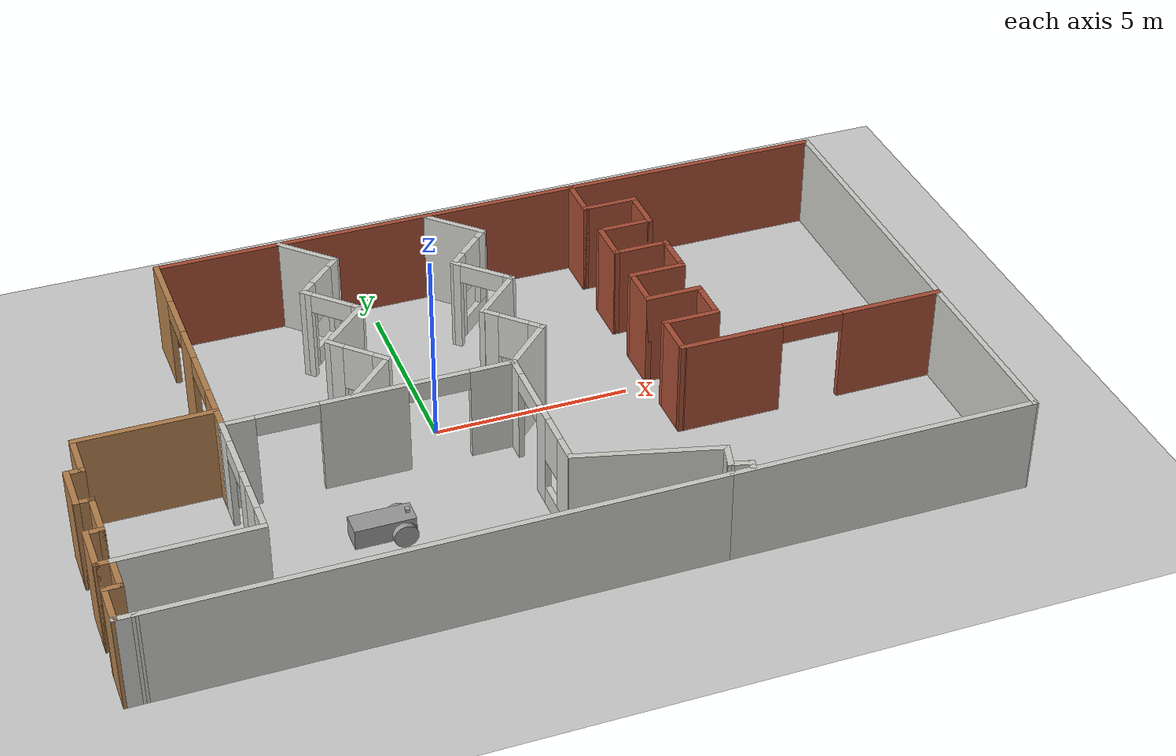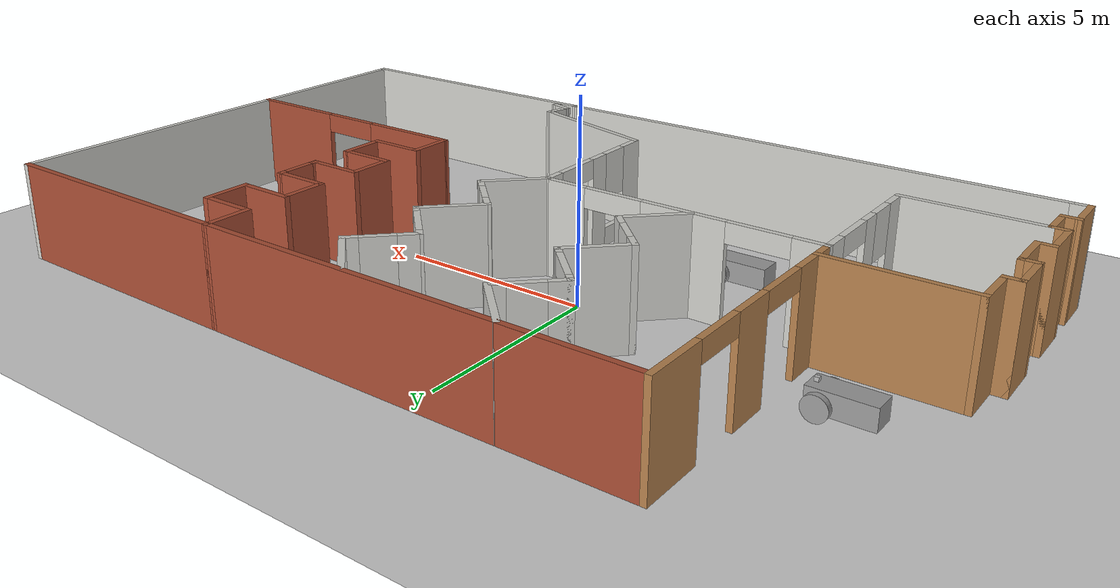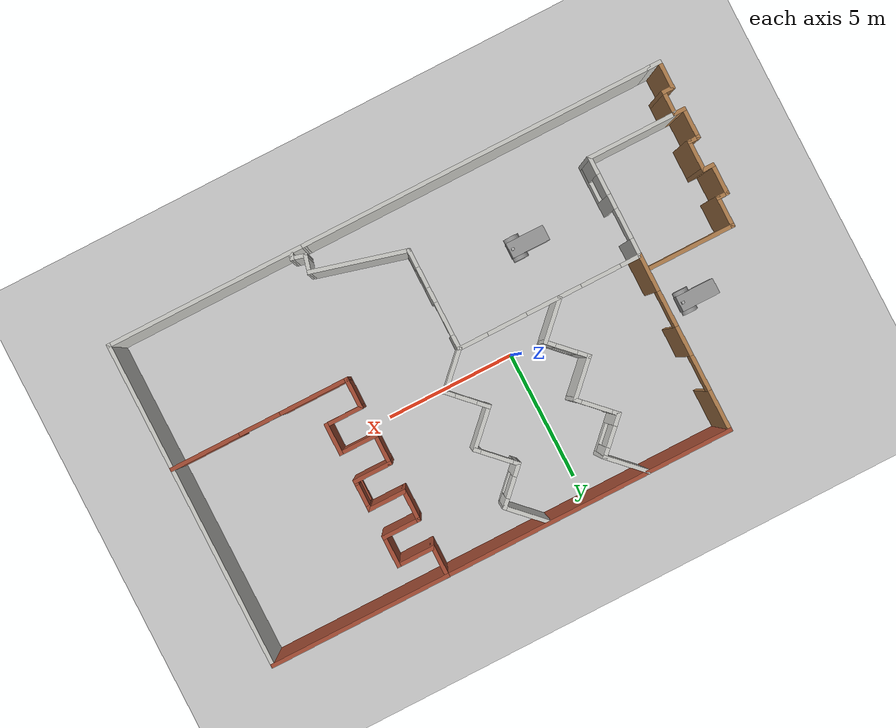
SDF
<sdf version="1.6">
 <world name="default">
  <plugin name="welcome_message" filename="libwelcome_message.so"/>
  <light name="sun" type="directional">
   <pose>0 0 10 0 -0 0</pose>
   <diffuse>0.8 0.8 0.8 1</diffuse>
   <specular>0.2 0.2 0.2 1</specular>
   <attenuation>
    <range>1000</range>
    <constant>0.9</constant>
    <linear>0.01</linear>
    <quadratic>0.001</quadratic>
   </attenuation>
   <direction>-0.5 0.1 -0.9</direction>
  </light>
  <model name="ground_plane">
   <static>1</static>
   <link name="link">
    <collision name="collision">
     <geometry><plane><normal>0 0 1</normal><size>100 100</size></plane></geometry>
     <surface>
      <contact><collide_bitmask>65535</collide_bitmask></contact>
      <friction><ode><mu>100</mu><mu2>50</mu2></ode></friction>
     </surface>
    </collision>
    <visual name="visual">
     <cast_shadows>0</cast_shadows>
     <geometry><plane><normal>0 0 1</normal><size>100 100</size></plane></geometry>
     <material>
      <script><uri>file://media/materials/scripts/gazebo.material</uri><name>Gazebo/Grey</name></script>
     </material>
    </visual>
   </link>
  </model>
  <gravity>0 0 -9.8</gravity>
  <magnetic_field>6e-06 2.3e-05 -4.2e-05</magnetic_field>
  <atmosphere type="adiabatic"/>
  <physics name="default_physics" default="0" type="ode">
   <max_step_size>0.001</max_step_size>
   <real_time_factor>1</real_time_factor>
   <real_time_update_rate>1000</real_time_update_rate>
  </physics>
  <scene><ambient>0.4 0.4 0.4 1</ambient><background>0.7 0.7 0.7 1</background><shadows>1</shadows></scene>
  <spherical_coordinates>
   <surface_model>EARTH_WGS84</surface_model>
   <latitude_deg>0</latitude_deg>
   <longitude_deg>0</longitude_deg>
   <elevation>0</elevation>
   <heading_deg>0</heading_deg>
  </spherical_coordinates>
  <model name="Building">
   <pose>1.68029 -0.499635 0 0 -0 0</pose>
   <link name="Wall_10">
    <collision name="Wall_10_Collision">
     <geometry><box><size>1.75 0.15 2.5</size></box></geometry>
     <pose>0 0 1.25 0 -0 0</pose>
    </collision>
    <visual name="Wall_10_Visual">
     <pose>0 0 1.25 0 -0 0</pose>
     <geometry><box><size>1.75 0.15 2.5</size></box></geometry>
     <material>
      <script><uri>file://media/materials/scripts/gazebo.material</uri><name>Gazebo/CeilingTiled</name></script>
      <ambient>0.819608 0.317647 0.317647 1</ambient>
     </material>
     <meta><layer>0</layer></meta>
    </visual>
    <pose>-3.36491 2.28919 0 0 -0 0.785398</pose>
   </link>
   <link name="Wall_101">
    <collision name="Wall_101_Collision">
     <geometry><box><size>3.69503 0.15 2.5</size></box></geometry>
     <pose>0 0 1.25 0 -0 0</pose>
    </collision>
    <visual name="Wall_101_Visual">
     <pose>0 0 1.25 0 -0 0</pose>
     <geometry><box><size>3.69503 0.15 2.5</size></box></geometry>
     <material>
      <script><uri>file://media/materials/scripts/gazebo.material</uri><name>Gazebo/CeilingTiled</name></script>
      <ambient>0.270588 0.431373 0.760784 1</ambient>
     </material>
     <meta><layer>0</layer></meta>
    </visual>
    <pose>1.71281 -4.90672 0 0 -0 2.88037</pose>
   </link>
   <link name="Wall_103">
    <collision name="Wall_103_Collision">
     <geometry><box><size>3.5 0.15 2.5</size></box></geometry>
     <pose>0 0 1.25 0 -0 0</pose>
    </collision>
    <visual name="Wall_103_Visual">
     <pose>0 0 1.25 0 -0 0</pose>
     <geometry><box><size>3.5 0.15 2.5</size></box></geometry>
     <material>
      <script><uri>file://media/materials/scripts/gazebo.material</uri><name>Gazebo/CeilingTiled</name></script>
      <ambient>0.901961 0.458824 0.458824 1</ambient>
     </material>
     <meta><layer>0</layer></meta>
    </visual>
    <pose>-8.79366 -4.43055 0 0 -0 3.14159</pose>
   </link>
   <link name="Wall_106">
    <collision name="Wall_106_Collision">
     <geometry><box><size>1 0.15 2.5</size></box></geometry>
     <pose>0 0 1.25 0 -0 0</pose>
    </collision>
    <visual name="Wall_106_Visual">
     <pose>0 0 1.25 0 -0 0</pose>
     <geometry><box><size>1 0.15 2.5</size></box></geometry>
     <material>
      <script><uri>file://media/materials/scripts/gazebo.material</uri><name>Gazebo/Wood</name></script>
      <ambient>1 1 1 1</ambient>
     </material>
     <meta><layer>0</layer></meta>
    </visual>
    <pose>-10.4687 -4.85555 0 0 -0 -1.5708</pose>
   </link>
   <link name="Wall_107">
    <collision name="Wall_107_Collision">
     <geometry><box><size>0.5 0.15 2.5</size></box></geometry>
     <pose>0 0 1.25 0 -0 0</pose>
    </collision>
    <visual name="Wall_107_Visual">
     <pose>0 0 1.25 0 -0 0</pose>
     <geometry><box><size>0.5 0.15 2.5</size></box></geometry>
     <material>
      <script><uri>file://media/materials/scripts/gazebo.material</uri><name>Gazebo/Wood</name></script>
      <ambient>1 1 1 1</ambient>
     </material>
     <meta><layer>0</layer></meta>
    </visual>
    <pose>-10.6437 -5.28055 0 0 -0 3.14159</pose>
   </link>
   <link name="Wall_109">
    <collision name="Wall_109_Collision">
     <geometry><box><size>1.14866 0.15 2.5</size></box></geometry>
     <pose>0 0 1.25 0 -0 0</pose>
    </collision>
    <visual name="Wall_109_Visual">
     <pose>0 0 1.25 0 -0 0</pose>
     <geometry><box><size>1.14866 0.15 2.5</size></box></geometry>
     <material>
      <script><uri>file://media/materials/scripts/gazebo.material</uri><name>Gazebo/Wood</name></script>
      <ambient>1 1 1 1</ambient>
     </material>
     <meta><layer>0</layer></meta>
    </visual>
    <pose>-10.8186 -5.77988 0 0 -0 -1.57071</pose>
   </link>
   <link name="Wall_11">
    <pose>-3.36491 3.42056 0 0 -0 2.35619</pose>
    <visual name="Wall_11_Visual_0">
     <pose>-0.725051 0 1.25 0 -0 0</pose>
     <geometry><box><size>0.299898 0.15 2.5</size></box></geometry>
     <material>
      <script><uri>file://media/materials/scripts/gazebo.material</uri><name>Gazebo/CeilingTiled</name></script>
      <ambient>0.819608 0.317647 0.317647 1</ambient>
     </material>
     <meta><layer>0</layer></meta>
    </visual>
    <collision name="Wall_11_Collision_0">
     <geometry><box><size>0.299898 0.15 2.5</size></box></geometry>
     <pose>-0.725051 0 1.25 0 -0 0</pose>
    </collision>
    <visual name="Wall_11_Visual_1">
     <pose>0.716913 0 1.25 0 -0 0</pose>
     <geometry><box><size>0.316173 0.15 2.5</size></box></geometry>
     <material>
      <script><uri>file://media/materials/scripts/gazebo.material</uri><name>Gazebo/CeilingTiled</name></script>
      <ambient>0.819608 0.317647 0.317647 1</ambient>
     </material>
     <meta><layer>0</layer></meta>
    </visual>
    <collision name="Wall_11_Collision_1">
     <geometry><box><size>0.316173 0.15 2.5</size></box></geometry>
     <pose>0.716913 0 1.25 0 -0 0</pose>
    </collision>
    <visual name="Wall_11_Visual_2">
     <pose>-0.008138 0 2.25 0 -0 0</pose>
     <geometry><box><size>1.13393 0.15 0.5</size></box></geometry>
     <material>
      <script><uri>file://media/materials/scripts/gazebo.material</uri><name>Gazebo/CeilingTiled</name></script>
      <ambient>0.819608 0.317647 0.317647 1</ambient>
     </material>
     <meta><layer>0</layer></meta>
    </visual>
    <collision name="Wall_11_Collision_2">
     <geometry><box><size>1.13393 0.15 0.5</size></box></geometry>
     <pose>-0.008138 0 2.25 0 -0 0</pose>
    </collision>
   </link>
   <link name="Wall_110">
    <collision name="Wall_110_Collision">
     <geometry><box><size>0.583483 0.15 2.5</size></box></geometry>
     <pose>0 0 1.25 0 -0 0</pose>
    </collision>
    <visual name="Wall_110_Visual">
     <pose>0 0 1.25 0 -0 0</pose>
     <geometry><box><size>0.583483 0.15 2.5</size></box></geometry>
     <material>
      <script><uri>file://media/materials/scripts/gazebo.material</uri><name>Gazebo/CeilingTiled</name></script>
      <ambient>0.760784 0.662745 0.627451 1</ambient>
     </material>
     <meta><layer>0</layer></meta>
    </visual>
    <pose>-10.6018 -6.27956 0 0 -0 -0.001671</pose>
   </link>
   <link name="Wall_113">
    <collision name="Wall_113_Collision">
     <geometry><box><size>0.5 0.15 2.5</size></box></geometry>
     <pose>0 0 1.25 0 -0 0</pose>
    </collision>
    <visual name="Wall_113_Visual">
     <pose>0 0 1.25 0 -0 0</pose>
     <geometry><box><size>0.5 0.15 2.5</size></box></geometry>
     <material>
      <script><uri>file://media/materials/scripts/gazebo.material</uri><name>Gazebo/Wood</name></script>
      <ambient>1 1 1 1</ambient>
     </material>
     <meta><layer>0</layer></meta>
    </visual>
    <pose>-10.6437 -4.43055 0 0 -0 3.14159</pose>
   </link>
   <link name="Wall_114">
    <collision name="Wall_114_Collision">
     <geometry><box><size>1.25 0.15 2.5</size></box></geometry>
     <pose>0 0 1.25 0 -0 0</pose>
    </collision>
    <visual name="Wall_114_Visual">
     <pose>0 0 1.25 0 -0 0</pose>
     <geometry><box><size>1.25 0.15 2.5</size></box></geometry>
     <material>
      <script><uri>file://media/materials/scripts/gazebo.material</uri><name>Gazebo/Wood</name></script>
      <ambient>1 1 1 1</ambient>
     </material>
     <meta><layer>0</layer></meta>
    </visual>
    <pose>-10.8187 -3.88055 0 0 -0 1.5708</pose>
   </link>
   <link name="Wall_115">
    <collision name="Wall_115_Collision">
     <geometry><box><size>0.5 0.15 2.5</size></box></geometry>
     <pose>0 0 1.25 0 -0 0</pose>
    </collision>
    <visual name="Wall_115_Visual">
     <pose>0 0 1.25 0 -0 0</pose>
     <geometry><box><size>0.5 0.15 2.5</size></box></geometry>
     <material>
      <script><uri>file://media/materials/scripts/gazebo.material</uri><name>Gazebo/Wood</name></script>
      <ambient>1 1 1 1</ambient>
     </material>
     <meta><layer>0</layer></meta>
    </visual>
    <pose>-10.6437 -3.33055 0 0 -0 0</pose>
   </link>
   <link name="Wall_116">
    <collision name="Wall_116_Collision">
     <geometry><box><size>1.25 0.15 2.5</size></box></geometry>
     <pose>0 0 1.25 0 -0 0</pose>
    </collision>
    <visual name="Wall_116_Visual">
     <pose>0 0 1.25 0 -0 0</pose>
     <geometry><box><size>1.25 0.15 2.5</size></box></geometry>
     <material>
      <script><uri>file://media/materials/scripts/gazebo.material</uri><name>Gazebo/Wood</name></script>
      <ambient>1 1 1 1</ambient>
     </material>
     <meta><layer>0</layer></meta>
    </visual>
    <pose>-10.4687 -2.78055 0 0 -0 1.5708</pose>
   </link>
   <link name="Wall_117">
    <collision name="Wall_117_Collision">
     <geometry><box><size>0.5 0.15 2.5</size></box></geometry>
     <pose>0 0 1.25 0 -0 0</pose>
    </collision>
    <visual name="Wall_117_Visual">
     <pose>0 0 1.25 0 -0 0</pose>
     <geometry><box><size>0.5 0.15 2.5</size></box></geometry>
     <material>
      <script><uri>file://media/materials/scripts/gazebo.material</uri><name>Gazebo/Wood</name></script>
      <ambient>1 1 1 1</ambient>
     </material>
     <meta><layer>0</layer></meta>
    </visual>
    <pose>-10.6437 -2.23055 0 0 -0 3.14159</pose>
   </link>
   <link name="Wall_118">
    <collision name="Wall_118_Collision">
     <geometry><box><size>1.25 0.15 2.5</size></box></geometry>
     <pose>0 0 1.25 0 -0 0</pose>
    </collision>
    <visual name="Wall_118_Visual">
     <pose>0 0 1.25 0 -0 0</pose>
     <geometry><box><size>1.25 0.15 2.5</size></box></geometry>
     <material>
      <script><uri>file://media/materials/scripts/gazebo.material</uri><name>Gazebo/Wood</name></script>
      <ambient>1 1 1 1</ambient>
     </material>
     <meta><layer>0</layer></meta>
    </visual>
    <pose>-10.8187 -1.68055 0 0 -0 1.5708</pose>
   </link>
   <link name="Wall_119">
    <collision name="Wall_119_Collision">
     <geometry><box><size>0.5 0.15 2.5</size></box></geometry>
     <pose>0 0 1.25 0 -0 0</pose>
    </collision>
    <visual name="Wall_119_Visual">
     <pose>0 0 1.25 0 -0 0</pose>
     <geometry><box><size>0.5 0.15 2.5</size></box></geometry>
     <material>
      <script><uri>file://media/materials/scripts/gazebo.material</uri><name>Gazebo/Wood</name></script>
      <ambient>1 1 1 1</ambient>
     </material>
     <meta><layer>0</layer></meta>
    </visual>
    <pose>-10.6437 -1.13055 0 0 -0 0</pose>
   </link>
   <link name="Wall_12">
    <pose>-3.36491 4.55193 0 0 -0 0.785398</pose>
    <visual name="Wall_12_Visual_0">
     <pose>-0.61476 0 1.25 0 -0 0</pose>
     <geometry><box><size>0.52048 0.15 2.5</size></box></geometry>
     <material>
      <script><uri>file://media/materials/scripts/gazebo.material</uri><name>Gazebo/CeilingTiled</name></script>
      <ambient>0.819608 0.317647 0.317647 1</ambient>
     </material>
     <meta><layer>0</layer></meta>
    </visual>
    <collision name="Wall_12_Collision_0">
     <geometry><box><size>0.52048 0.15 2.5</size></box></geometry>
     <pose>-0.61476 0 1.25 0 -0 0</pose>
    </collision>
    <visual name="Wall_12_Visual_1">
     <pose>0.26024 0 0.25 0 -0 0</pose>
     <geometry><box><size>1.22952 0.15 0.5</size></box></geometry>
     <material>
      <script><uri>file://media/materials/scripts/gazebo.material</uri><name>Gazebo/CeilingTiled</name></script>
      <ambient>0.819608 0.317647 0.317647 1</ambient>
     </material>
     <meta><layer>0</layer></meta>
    </visual>
    <collision name="Wall_12_Collision_1">
     <geometry><box><size>1.22952 0.15 0.5</size></box></geometry>
     <pose>0.26024 0 0.25 0 -0 0</pose>
    </collision>
    <visual name="Wall_12_Visual_2">
     <pose>0.66024 0 1.5 0 -0 0</pose>
     <geometry><box><size>0.42952 0.15 2</size></box></geometry>
     <material>
      <script><uri>file://media/materials/scripts/gazebo.material</uri><name>Gazebo/CeilingTiled</name></script>
      <ambient>0.819608 0.317647 0.317647 1</ambient>
     </material>
     <meta><layer>0</layer></meta>
    </visual>
    <collision name="Wall_12_Collision_2">
     <geometry><box><size>0.42952 0.15 2</size></box></geometry>
     <pose>0.66024 0 1.5 0 -0 0</pose>
    </collision>
    <visual name="Wall_12_Visual_3">
     <pose>0.04548 0 1.9 0 -0 0</pose>
     <geometry><box><size>0.8 0.15 1.2</size></box></geometry>
     <material>
      <script><uri>file://media/materials/scripts/gazebo.material</uri><name>Gazebo/CeilingTiled</name></script>
      <ambient>0.819608 0.317647 0.317647 1</ambient>
     </material>
     <meta><layer>0</layer></meta>
    </visual>
    <collision name="Wall_12_Collision_3">
     <geometry><box><size>0.8 0.15 1.2</size></box></geometry>
     <pose>0.04548 0 1.9 0 -0 0</pose>
    </collision>
   </link>
   <link name="Wall_120">
    <collision name="Wall_120_Collision">
     <geometry><box><size>1.25 0.15 2.5</size></box></geometry>
     <pose>0 0 1.25 0 -0 0</pose>
    </collision>
    <visual name="Wall_120_Visual">
     <pose>0 0 1.25 0 -0 0</pose>
     <geometry><box><size>1.25 0.15 2.5</size></box></geometry>
     <material>
      <script><uri>file://media/materials/scripts/gazebo.material</uri><name>Gazebo/Wood</name></script>
      <ambient>1 1 1 1</ambient>
     </material>
     <meta><layer>0</layer></meta>
    </visual>
    <pose>-10.4687 -0.580548 0 0 -0 1.5708</pose>
   </link>
   <link name="Wall_121">
    <collision name="Wall_121_Collision">
     <geometry><box><size>3.5 0.15 2.5</size></box></geometry>
     <pose>0 0 1.25 0 -0 0</pose>
    </collision>
    <visual name="Wall_121_Visual">
     <pose>0 0 1.25 0 -0 0</pose>
     <geometry><box><size>3.5 0.15 2.5</size></box></geometry>
     <material>
      <script><uri>file://media/materials/scripts/gazebo.material</uri><name>Gazebo/Wood</name></script>
      <ambient>1 1 1 1</ambient>
     </material>
     <meta><layer>0</layer></meta>
    </visual>
    <pose>-8.79366 -0.030549 0 0 -0 0</pose>
   </link>
   <link name="Wall_14">
    <collision name="Wall_14_Collision">
     <geometry><box><size>1.75 0.15 2.5</size></box></geometry>
     <pose>0 0 1.25 0 -0 0</pose>
    </collision>
    <visual name="Wall_14_Visual">
     <pose>0 0 1.25 0 -0 0</pose>
     <geometry><box><size>1.75 0.15 2.5</size></box></geometry>
     <material>
      <script><uri>file://media/materials/scripts/gazebo.material</uri><name>Gazebo/CeilingTiled</name></script>
      <ambient>0.819608 0.317647 0.317647 1</ambient>
     </material>
     <meta><layer>0</layer></meta>
    </visual>
    <pose>-3.36491 5.6833 0 0 -0 2.35619</pose>
   </link>
   <link name="Wall_18">
    <pose>-7.11866 -2.50555 0 0 -0 -1.5708</pose>
    <visual name="Wall_18_Visual_0">
     <pose>-1.63024 0 1.25 0 -0 0</pose>
     <geometry><box><size>0.739525 0.15 2.5</size></box></geometry>
     <material>
      <script><uri>file://media/materials/scripts/gazebo.material</uri><name>Gazebo/CeilingTiled</name></script>
      <ambient>0.901961 0.458824 0.458824 1</ambient>
     </material>
     <meta><layer>0</layer></meta>
    </visual>
    <collision name="Wall_18_Collision_0">
     <geometry><box><size>0.739525 0.15 2.5</size></box></geometry>
     <pose>-1.63024 0 1.25 0 -0 0</pose>
    </collision>
    <visual name="Wall_18_Visual_1">
     <pose>0.19611 0 1.25 0 -0 0</pose>
     <geometry><box><size>0.547855 0.15 2.5</size></box></geometry>
     <material>
      <script><uri>file://media/materials/scripts/gazebo.material</uri><name>Gazebo/CeilingTiled</name></script>
      <ambient>0.901961 0.458824 0.458824 1</ambient>
     </material>
     <meta><layer>0</layer></meta>
    </visual>
    <collision name="Wall_18_Collision_1">
     <geometry><box><size>0.547855 0.15 2.5</size></box></geometry>
     <pose>0.19611 0 1.25 0 -0 0</pose>
    </collision>
    <visual name="Wall_18_Visual_2">
     <pose>1.23502 0 0.25 0 -0 0</pose>
     <geometry><box><size>1.52996 0.15 0.5</size></box></geometry>
     <material>
      <script><uri>file://media/materials/scripts/gazebo.material</uri><name>Gazebo/CeilingTiled</name></script>
      <ambient>0.901961 0.458824 0.458824 1</ambient>
     </material>
     <meta><layer>0</layer></meta>
    </visual>
    <collision name="Wall_18_Collision_2">
     <geometry><box><size>1.52996 0.15 0.5</size></box></geometry>
     <pose>1.23502 0 0.25 0 -0 0</pose>
    </collision>
    <visual name="Wall_18_Visual_3">
     <pose>1.63502 0 1.5 0 -0 0</pose>
     <geometry><box><size>0.729962 0.15 2</size></box></geometry>
     <material>
      <script><uri>file://media/materials/scripts/gazebo.material</uri><name>Gazebo/CeilingTiled</name></script>
      <ambient>0.901961 0.458824 0.458824 1</ambient>
     </material>
     <meta><layer>0</layer></meta>
    </visual>
    <collision name="Wall_18_Collision_3">
     <geometry><box><size>0.729962 0.15 2</size></box></geometry>
     <pose>1.63502 0 1.5 0 -0 0</pose>
    </collision>
    <visual name="Wall_18_Visual_4">
     <pose>0.870038 0 1.9 0 -0 0</pose>
     <geometry><box><size>0.8 0.15 1.2</size></box></geometry>
     <material>
      <script><uri>file://media/materials/scripts/gazebo.material</uri><name>Gazebo/CeilingTiled</name></script>
      <ambient>0.901961 0.458824 0.458824 1</ambient>
     </material>
     <meta><layer>0</layer></meta>
    </visual>
    <collision name="Wall_18_Collision_4">
     <geometry><box><size>0.8 0.15 1.2</size></box></geometry>
     <pose>0.870038 0 1.9 0 -0 0</pose>
    </collision>
    <visual name="Wall_18_Visual_5">
     <pose>-0.669147 0 2.25 0 -0 0</pose>
     <geometry><box><size>1.18266 0.15 0.5</size></box></geometry>
     <material>
      <script><uri>file://media/materials/scripts/gazebo.material</uri><name>Gazebo/CeilingTiled</name></script>
      <ambient>0.901961 0.458824 0.458824 1</ambient>
     </material>
     <meta><layer>0</layer></meta>
    </visual>
    <collision name="Wall_18_Collision_5">
     <geometry><box><size>1.18266 0.15 0.5</size></box></geometry>
     <pose>-0.669147 0 2.25 0 -0 0</pose>
    </collision>
   </link>
   <link name="Wall_21">
    <pose>-0.018662 -2.50555 0 0 -0 -1.5708</pose>
    <visual name="Wall_21_Visual_0">
     <pose>-1.69808 0 1.25 0 -0 0</pose>
     <geometry><box><size>0.603849 0.15 2.5</size></box></geometry>
     <material>
      <script><uri>file://media/materials/scripts/gazebo.material</uri><name>Gazebo/CeilingTiled</name></script>
      <ambient>0.270588 0.431373 0.760784 1</ambient>
     </material>
     <meta><layer>0</layer></meta>
    </visual>
    <collision name="Wall_21_Collision_0">
     <geometry><box><size>0.603849 0.15 2.5</size></box></geometry>
     <pose>-1.69808 0 1.25 0 -0 0</pose>
    </collision>
    <visual name="Wall_21_Visual_1">
     <pose>0.184804 0 1.25 0 -0 0</pose>
     <geometry><box><size>0.570468 0.15 2.5</size></box></geometry>
     <material>
      <script><uri>file://media/materials/scripts/gazebo.material</uri><name>Gazebo/CeilingTiled</name></script>
      <ambient>0.270588 0.431373 0.760784 1</ambient>
     </material>
     <meta><layer>0</layer></meta>
    </visual>
    <collision name="Wall_21_Collision_1">
     <geometry><box><size>0.570468 0.15 2.5</size></box></geometry>
     <pose>0.184804 0 1.25 0 -0 0</pose>
    </collision>
    <visual name="Wall_21_Visual_2">
     <pose>1.23502 0 0.25 0 -0 0</pose>
     <geometry><box><size>1.52996 0.15 0.5</size></box></geometry>
     <material>
      <script><uri>file://media/materials/scripts/gazebo.material</uri><name>Gazebo/CeilingTiled</name></script>
      <ambient>0.270588 0.431373 0.760784 1</ambient>
     </material>
     <meta><layer>0</layer></meta>
    </visual>
    <collision name="Wall_21_Collision_2">
     <geometry><box><size>1.52996 0.15 0.5</size></box></geometry>
     <pose>1.23502 0 0.25 0 -0 0</pose>
    </collision>
    <visual name="Wall_21_Visual_3">
     <pose>1.63502 0 1.5 0 -0 0</pose>
     <geometry><box><size>0.729962 0.15 2</size></box></geometry>
     <material>
      <script><uri>file://media/materials/scripts/gazebo.material</uri><name>Gazebo/CeilingTiled</name></script>
      <ambient>0.270588 0.431373 0.760784 1</ambient>
     </material>
     <meta><layer>0</layer></meta>
    </visual>
    <collision name="Wall_21_Collision_3">
     <geometry><box><size>0.729962 0.15 2</size></box></geometry>
     <pose>1.63502 0 1.5 0 -0 0</pose>
    </collision>
    <visual name="Wall_21_Visual_4">
     <pose>0.870038 0 1.9 0 -0 0</pose>
     <geometry><box><size>0.8 0.15 1.2</size></box></geometry>
     <material>
      <script><uri>file://media/materials/scripts/gazebo.material</uri><name>Gazebo/CeilingTiled</name></script>
      <ambient>0.270588 0.431373 0.760784 1</ambient>
     </material>
     <meta><layer>0</layer></meta>
    </visual>
    <collision name="Wall_21_Collision_4">
     <geometry><box><size>0.8 0.15 1.2</size></box></geometry>
     <pose>0.870038 0 1.9 0 -0 0</pose>
    </collision>
    <visual name="Wall_21_Visual_5">
     <pose>-0.748291 0 2.25 0 -0 0</pose>
     <geometry><box><size>1.29572 0.15 0.5</size></box></geometry>
     <material>
      <script><uri>file://media/materials/scripts/gazebo.material</uri><name>Gazebo/CeilingTiled</name></script>
      <ambient>0.270588 0.431373 0.760784 1</ambient>
     </material>
     <meta><layer>0</layer></meta>
    </visual>
    <collision name="Wall_21_Collision_5">
     <geometry><box><size>1.29572 0.15 0.5</size></box></geometry>
     <pose>-0.748291 0 2.25 0 -0 0</pose>
    </collision>
   </link>
   <link name="Wall_4">
    <pose>-3.36491 1.15782 0 0 -0 -0.785398</pose>
    <visual name="Wall_4_Visual_0">
     <pose>-0.622738 0 1.25 0 -0 0</pose>
     <geometry><box><size>0.504524 0.15 2.5</size></box></geometry>
     <material>
      <script><uri>file://media/materials/scripts/gazebo.material</uri><name>Gazebo/CeilingTiled</name></script>
      <ambient>0.819608 0.317647 0.317647 1</ambient>
     </material>
     <meta><layer>0</layer></meta>
    </visual>
    <collision name="Wall_4_Collision_0">
     <geometry><box><size>0.504524 0.15 2.5</size></box></geometry>
     <pose>-0.622738 0 1.25 0 -0 0</pose>
    </collision>
    <visual name="Wall_4_Visual_1">
     <pose>0.252262 0 0.25 0 -0 0</pose>
     <geometry><box><size>1.24548 0.15 0.5</size></box></geometry>
     <material>
      <script><uri>file://media/materials/scripts/gazebo.material</uri><name>Gazebo/CeilingTiled</name></script>
      <ambient>0.819608 0.317647 0.317647 1</ambient>
     </material>
     <meta><layer>0</layer></meta>
    </visual>
    <collision name="Wall_4_Collision_1">
     <geometry><box><size>1.24548 0.15 0.5</size></box></geometry>
     <pose>0.252262 0 0.25 0 -0 0</pose>
    </collision>
    <visual name="Wall_4_Visual_2">
     <pose>0.652262 0 1.5 0 -0 0</pose>
     <geometry><box><size>0.445476 0.15 2</size></box></geometry>
     <material>
      <script><uri>file://media/materials/scripts/gazebo.material</uri><name>Gazebo/CeilingTiled</name></script>
      <ambient>0.819608 0.317647 0.317647 1</ambient>
     </material>
     <meta><layer>0</layer></meta>
    </visual>
    <collision name="Wall_4_Collision_2">
     <geometry><box><size>0.445476 0.15 2</size></box></geometry>
     <pose>0.652262 0 1.5 0 -0 0</pose>
    </collision>
    <visual name="Wall_4_Visual_3">
     <pose>0.029524 0 1.9 0 -0 0</pose>
     <geometry><box><size>0.8 0.15 1.2</size></box></geometry>
     <material>
      <script><uri>file://media/materials/scripts/gazebo.material</uri><name>Gazebo/CeilingTiled</name></script>
      <ambient>0.819608 0.317647 0.317647 1</ambient>
     </material>
     <meta><layer>0</layer></meta>
    </visual>
    <collision name="Wall_4_Collision_3">
     <geometry><box><size>0.8 0.15 1.2</size></box></geometry>
     <pose>0.029524 0 1.9 0 -0 0</pose>
    </collision>
   </link>
   <link name="Wall_43">
    <collision name="Wall_43_Collision">
     <geometry><box><size>13.7085 0.15 2.5</size></box></geometry>
     <pose>0 0 1.25 0 -0 0</pose>
    </collision>
    <visual name="Wall_43_Visual">
     <pose>0 0 1.25 0 -0 0</pose>
     <geometry><box><size>13.7085 0.15 2.5</size></box></geometry>
     <material>
      <script><uri>file://media/materials/scripts/gazebo.material</uri><name>Gazebo/CeilingTiled</name></script>
      <ambient>0.760784 0.662745 0.627451 1</ambient>
     </material>
     <meta><layer>0</layer></meta>
    </visual>
    <pose>-3.60582 -6.27971 0 0 -0 3.2e-05</pose>
   </link>
   <link name="Wall_48">
    <collision name="Wall_48_Collision">
     <geometry><box><size>1.75 0.15 2.5</size></box></geometry>
     <pose>0 0 1.25 0 -0 0</pose>
    </collision>
    <visual name="Wall_48_Visual">
     <pose>0 0 1.25 0 -0 0</pose>
     <geometry><box><size>1.75 0.15 2.5</size></box></geometry>
     <material>
      <script><uri>file://media/materials/scripts/gazebo.material</uri><name>Gazebo/CeilingTiled</name></script>
      <ambient>0.447059 0.623529 0.811765 1</ambient>
     </material>
     <meta><layer>0</layer></meta>
    </visual>
    <pose>0.547024 -0.014863 0 0 -0 0.785398</pose>
   </link>
   <link name="Wall_5">
    <collision name="Wall_5_Collision">
     <geometry><box><size>1.75 0.15 2.5</size></box></geometry>
     <pose>0 0 1.25 0 -0 0</pose>
    </collision>
    <visual name="Wall_5_Visual">
     <pose>0 0 1.25 0 -0 0</pose>
     <geometry><box><size>1.75 0.15 2.5</size></box></geometry>
     <material>
      <script><uri>file://media/materials/scripts/gazebo.material</uri><name>Gazebo/CeilingTiled</name></script>
      <ambient>0.819608 0.317647 0.317647 1</ambient>
     </material>
     <meta><layer>0</layer></meta>
    </visual>
    <pose>-3.36491 0.026446 0 0 -0 -2.35619</pose>
   </link>
   <link name="Wall_50">
    <pose>0.551323 1.11651 0 0 -0 2.35238</pose>
    <visual name="Wall_50_Visual_0">
     <pose>-0.655708 0 1.25 0 -0 0</pose>
     <geometry><box><size>0.432515 0.15 2.5</size></box></geometry>
     <material>
      <script><uri>file://media/materials/scripts/gazebo.material</uri><name>Gazebo/CeilingTiled</name></script>
      <ambient>0.447059 0.623529 0.811765 1</ambient>
     </material>
     <meta><layer>0</layer></meta>
    </visual>
    <collision name="Wall_50_Collision_0">
     <geometry><box><size>0.432515 0.15 2.5</size></box></geometry>
     <pose>-0.655708 0 1.25 0 -0 0</pose>
    </collision>
    <visual name="Wall_50_Visual_1">
     <pose>0.216258 0 0.25 0 -0 0</pose>
     <geometry><box><size>1.31142 0.15 0.5</size></box></geometry>
     <material>
      <script><uri>file://media/materials/scripts/gazebo.material</uri><name>Gazebo/CeilingTiled</name></script>
      <ambient>0.447059 0.623529 0.811765 1</ambient>
     </material>
     <meta><layer>0</layer></meta>
    </visual>
    <collision name="Wall_50_Collision_1">
     <geometry><box><size>1.31142 0.15 0.5</size></box></geometry>
     <pose>0.216258 0 0.25 0 -0 0</pose>
    </collision>
    <visual name="Wall_50_Visual_2">
     <pose>0.616258 0 1.5 0 -0 0</pose>
     <geometry><box><size>0.511417 0.15 2</size></box></geometry>
     <material>
      <script><uri>file://media/materials/scripts/gazebo.material</uri><name>Gazebo/CeilingTiled</name></script>
      <ambient>0.447059 0.623529 0.811765 1</ambient>
     </material>
     <meta><layer>0</layer></meta>
    </visual>
    <collision name="Wall_50_Collision_2">
     <geometry><box><size>0.511417 0.15 2</size></box></geometry>
     <pose>0.616258 0 1.5 0 -0 0</pose>
    </collision>
    <visual name="Wall_50_Visual_3">
     <pose>-0.039451 0 1.9 0 -0 0</pose>
     <geometry><box><size>0.8 0.15 1.2</size></box></geometry>
     <material>
      <script><uri>file://media/materials/scripts/gazebo.material</uri><name>Gazebo/CeilingTiled</name></script>
      <ambient>0.447059 0.623529 0.811765 1</ambient>
     </material>
     <meta><layer>0</layer></meta>
    </visual>
    <collision name="Wall_50_Collision_3">
     <geometry><box><size>0.8 0.15 1.2</size></box></geometry>
     <pose>-0.039451 0 1.9 0 -0 0</pose>
    </collision>
   </link>
   <link name="Wall_51">
    <collision name="Wall_51_Collision">
     <geometry><box><size>1.75 0.15 2.5</size></box></geometry>
     <pose>0 0 1.25 0 -0 0</pose>
    </collision>
    <visual name="Wall_51_Visual">
     <pose>0 0 1.25 0 -0 0</pose>
     <geometry><box><size>1.75 0.15 2.5</size></box></geometry>
     <material>
      <script><uri>file://media/materials/scripts/gazebo.material</uri><name>Gazebo/CeilingTiled</name></script>
      <ambient>0.447059 0.623529 0.811765 1</ambient>
     </material>
     <meta><layer>0</layer></meta>
    </visual>
    <pose>0.547024 2.23928 0 0 -0 0.785398</pose>
   </link>
   <link name="Wall_53">
    <pose>0.547024 3.37065 0 0 -0 2.35619</pose>
    <visual name="Wall_53_Visual_0">
     <pose>-0.730842 0 1.25 0 -0 0</pose>
     <geometry><box><size>0.288315 0.15 2.5</size></box></geometry>
     <material>
      <script><uri>file://media/materials/scripts/gazebo.material</uri><name>Gazebo/CeilingTiled</name></script>
      <ambient>0.447059 0.623529 0.811765 1</ambient>
     </material>
     <meta><layer>0</layer></meta>
    </visual>
    <collision name="Wall_53_Collision_0">
     <geometry><box><size>0.288315 0.15 2.5</size></box></geometry>
     <pose>-0.730842 0 1.25 0 -0 0</pose>
    </collision>
    <visual name="Wall_53_Visual_1">
     <pose>0.737705 0 1.25 0 -0 0</pose>
     <geometry><box><size>0.274591 0.15 2.5</size></box></geometry>
     <material>
      <script><uri>file://media/materials/scripts/gazebo.material</uri><name>Gazebo/CeilingTiled</name></script>
      <ambient>0.447059 0.623529 0.811765 1</ambient>
     </material>
     <meta><layer>0</layer></meta>
    </visual>
    <collision name="Wall_53_Collision_1">
     <geometry><box><size>0.274591 0.15 2.5</size></box></geometry>
     <pose>0.737705 0 1.25 0 -0 0</pose>
    </collision>
    <visual name="Wall_53_Visual_2">
     <pose>0.006862 0 2.25 0 -0 0</pose>
     <geometry><box><size>1.18709 0.15 0.5</size></box></geometry>
     <material>
      <script><uri>file://media/materials/scripts/gazebo.material</uri><name>Gazebo/CeilingTiled</name></script>
      <ambient>0.447059 0.623529 0.811765 1</ambient>
     </material>
     <meta><layer>0</layer></meta>
    </visual>
    <collision name="Wall_53_Collision_2">
     <geometry><box><size>1.18709 0.15 0.5</size></box></geometry>
     <pose>0.006862 0 2.25 0 -0 0</pose>
    </collision>
   </link>
   <link name="Wall_54">
    <pose>0.547024 4.50632 0 0 -0 0.789183</pose>
    <visual name="Wall_54_Visual_0">
     <pose>-0.605285 0 1.25 0 -0 0</pose>
     <geometry><box><size>0.545521 0.15 2.5</size></box></geometry>
     <material>
      <script><uri>file://media/materials/scripts/gazebo.material</uri><name>Gazebo/CeilingTiled</name></script>
      <ambient>0.447059 0.623529 0.811765 1</ambient>
     </material>
     <meta><layer>0</layer></meta>
    </visual>
    <collision name="Wall_54_Collision_0">
     <geometry><box><size>0.545521 0.15 2.5</size></box></geometry>
     <pose>-0.605285 0 1.25 0 -0 0</pose>
    </collision>
    <visual name="Wall_54_Visual_1">
     <pose>0.272761 0 0.25 0 -0 0</pose>
     <geometry><box><size>1.21057 0.15 0.5</size></box></geometry>
     <material>
      <script><uri>file://media/materials/scripts/gazebo.material</uri><name>Gazebo/CeilingTiled</name></script>
      <ambient>0.447059 0.623529 0.811765 1</ambient>
     </material>
     <meta><layer>0</layer></meta>
    </visual>
    <collision name="Wall_54_Collision_1">
     <geometry><box><size>1.21057 0.15 0.5</size></box></geometry>
     <pose>0.272761 0 0.25 0 -0 0</pose>
    </collision>
    <visual name="Wall_54_Visual_2">
     <pose>0.672761 0 1.5 0 -0 0</pose>
     <geometry><box><size>0.41057 0.15 2</size></box></geometry>
     <material>
      <script><uri>file://media/materials/scripts/gazebo.material</uri><name>Gazebo/CeilingTiled</name></script>
      <ambient>0.447059 0.623529 0.811765 1</ambient>
     </material>
     <meta><layer>0</layer></meta>
    </visual>
    <collision name="Wall_54_Collision_2">
     <geometry><box><size>0.41057 0.15 2</size></box></geometry>
     <pose>0.672761 0 1.5 0 -0 0</pose>
    </collision>
    <visual name="Wall_54_Visual_3">
     <pose>0.067476 0 1.9 0 -0 0</pose>
     <geometry><box><size>0.8 0.15 1.2</size></box></geometry>
     <material>
      <script><uri>file://media/materials/scripts/gazebo.material</uri><name>Gazebo/CeilingTiled</name></script>
      <ambient>0.447059 0.623529 0.811765 1</ambient>
     </material>
     <meta><layer>0</layer></meta>
    </visual>
    <collision name="Wall_54_Collision_3">
     <geometry><box><size>0.8 0.15 1.2</size></box></geometry>
     <pose>0.067476 0 1.9 0 -0 0</pose>
    </collision>
   </link>
   <link name="Wall_55">
    <collision name="Wall_55_Collision">
     <geometry><box><size>1.75 0.15 2.5</size></box></geometry>
     <pose>0 0 1.25 0 -0 0</pose>
    </collision>
    <visual name="Wall_55_Visual">
     <pose>0 0 1.25 0 -0 0</pose>
     <geometry><box><size>1.75 0.15 2.5</size></box></geometry>
     <material>
      <script><uri>file://media/materials/scripts/gazebo.material</uri><name>Gazebo/CeilingTiled</name></script>
      <ambient>0.447059 0.623529 0.811765 1</ambient>
     </material>
     <meta><layer>0</layer></meta>
    </visual>
    <pose>0.547024 5.64199 0 0 -0 2.35619</pose>
   </link>
   <link name="Wall_61">
    <pose>-7.11866 2.84445 0 0 -0 1.5708</pose>
    <visual name="Wall_61_Visual_0">
     <pose>-2.76325 0 1.25 0 -0 0</pose>
     <geometry><box><size>1.4735 0.15 2.5</size></box></geometry>
     <material>
      <script><uri>file://media/materials/scripts/gazebo.material</uri><name>Gazebo/Wood</name></script>
      <ambient>1 1 1 1</ambient>
     </material>
     <meta><layer>0</layer></meta>
    </visual>
    <collision name="Wall_61_Collision_0">
     <geometry><box><size>1.4735 0.15 2.5</size></box></geometry>
     <pose>-2.76325 0 1.25 0 -0 0</pose>
    </collision>
    <visual name="Wall_61_Visual_1">
     <pose>-0.068748 0 1.25 0 -0 0</pose>
     <geometry><box><size>1.14159 0.15 2.5</size></box></geometry>
     <material>
      <script><uri>file://media/materials/scripts/gazebo.material</uri><name>Gazebo/Wood</name></script>
      <ambient>1 1 1 1</ambient>
     </material>
     <meta><layer>0</layer></meta>
    </visual>
    <collision name="Wall_61_Collision_1">
     <geometry><box><size>1.14159 0.15 2.5</size></box></geometry>
     <pose>-0.068748 0 1.25 0 -0 0</pose>
    </collision>
    <visual name="Wall_61_Visual_2">
     <pose>2.68581 0 1.25 0 -0 0</pose>
     <geometry><box><size>1.62839 0.15 2.5</size></box></geometry>
     <material>
      <script><uri>file://media/materials/scripts/gazebo.material</uri><name>Gazebo/Wood</name></script>
      <ambient>1 1 1 1</ambient>
     </material>
     <meta><layer>0</layer></meta>
    </visual>
    <collision name="Wall_61_Collision_2">
     <geometry><box><size>1.62839 0.15 2.5</size></box></geometry>
     <pose>2.68581 0 1.25 0 -0 0</pose>
    </collision>
    <visual name="Wall_61_Visual_3">
     <pose>-1.33302 0 2.25 0 -0 0</pose>
     <geometry><box><size>1.38696 0.15 0.5</size></box></geometry>
     <material>
      <script><uri>file://media/materials/scripts/gazebo.material</uri><name>Gazebo/Wood</name></script>
      <ambient>1 1 1 1</ambient>
     </material>
     <meta><layer>0</layer></meta>
    </visual>
    <collision name="Wall_61_Collision_3">
     <geometry><box><size>1.38696 0.15 0.5</size></box></geometry>
     <pose>-1.33302 0 2.25 0 -0 0</pose>
    </collision>
    <visual name="Wall_61_Visual_4">
     <pose>1.18683 0 2.25 0 -0 0</pose>
     <geometry><box><size>1.36956 0.15 0.5</size></box></geometry>
     <material>
      <script><uri>file://media/materials/scripts/gazebo.material</uri><name>Gazebo/Wood</name></script>
      <ambient>1 1 1 1</ambient>
     </material>
     <meta><layer>0</layer></meta>
    </visual>
    <collision name="Wall_61_Collision_4">
     <geometry><box><size>1.36956 0.15 0.5</size></box></geometry>
     <pose>1.18683 0 2.25 0 -0 0</pose>
    </collision>
   </link>
   <link name="Wall_62">
    <collision name="Wall_62_Collision">
     <geometry><box><size>11.25 0.15 2.5</size></box></geometry>
     <pose>0 0 1.25 0 -0 0</pose>
    </collision>
    <visual name="Wall_62_Visual">
     <pose>0 0 1.25 0 -0 0</pose>
     <geometry><box><size>11.25 0.15 2.5</size></box></geometry>
     <material>
      <script><uri>file://media/materials/scripts/gazebo.material</uri><name>Gazebo/Bricks</name></script>
      <ambient>1 1 1 1</ambient>
     </material>
     <meta><layer>0</layer></meta>
    </visual>
    <pose>-1.56866 6.26945 0 0 -0 0</pose>
   </link>
   <link name="Wall_64">
    <collision name="Wall_64_Collision">
     <geometry><box><size>1.25 0.15 2.5</size></box></geometry>
     <pose>0 0 1.25 0 -0 0</pose>
    </collision>
    <visual name="Wall_64_Visual">
     <pose>0 0 1.25 0 -0 0</pose>
     <geometry><box><size>1.25 0.15 2.5</size></box></geometry>
     <material>
      <script><uri>file://media/materials/scripts/gazebo.material</uri><name>Gazebo/Bricks</name></script>
      <ambient>1 1 1 1</ambient>
     </material>
     <meta><layer>0</layer></meta>
    </visual>
    <pose>3.98134 5.71945 0 0 -0 -1.5708</pose>
   </link>
   <link name="Wall_65">
    <collision name="Wall_65_Collision">
     <geometry><box><size>1.5 0.15 2.5</size></box></geometry>
     <pose>0 0 1.25 0 -0 0</pose>
    </collision>
    <visual name="Wall_65_Visual">
     <pose>0 0 1.25 0 -0 0</pose>
     <geometry><box><size>1.5 0.15 2.5</size></box></geometry>
     <material>
      <script><uri>file://media/materials/scripts/gazebo.material</uri><name>Gazebo/Bricks</name></script>
      <ambient>1 1 1 1</ambient>
     </material>
     <meta><layer>0</layer></meta>
    </visual>
    <pose>4.65634 5.16945 0 0 -0 0</pose>
   </link>
   <link name="Wall_66">
    <collision name="Wall_66_Collision">
     <geometry><box><size>1.25 0.15 2.5</size></box></geometry>
     <pose>0 0 1.25 0 -0 0</pose>
    </collision>
    <visual name="Wall_66_Visual">
     <pose>0 0 1.25 0 -0 0</pose>
     <geometry><box><size>1.25 0.15 2.5</size></box></geometry>
     <material>
      <script><uri>file://media/materials/scripts/gazebo.material</uri><name>Gazebo/Bricks</name></script>
      <ambient>1 1 1 1</ambient>
     </material>
     <meta><layer>0</layer></meta>
    </visual>
    <pose>5.33134 4.61945 0 0 -0 -1.5708</pose>
   </link>
   <link name="Wall_67">
    <collision name="Wall_67_Collision">
     <geometry><box><size>1.5 0.15 2.5</size></box></geometry>
     <pose>0 0 1.25 0 -0 0</pose>
    </collision>
    <visual name="Wall_67_Visual">
     <pose>0 0 1.25 0 -0 0</pose>
     <geometry><box><size>1.5 0.15 2.5</size></box></geometry>
     <material>
      <script><uri>file://media/materials/scripts/gazebo.material</uri><name>Gazebo/Bricks</name></script>
      <ambient>1 1 1 1</ambient>
     </material>
     <meta><layer>0</layer></meta>
    </visual>
    <pose>4.65634 4.06945 0 0 -0 3.14159</pose>
   </link>
   <link name="Wall_68">
    <collision name="Wall_68_Collision">
     <geometry><box><size>1.25 0.15 2.5</size></box></geometry>
     <pose>0 0 1.25 0 -0 0</pose>
    </collision>
    <visual name="Wall_68_Visual">
     <pose>0 0 1.25 0 -0 0</pose>
     <geometry><box><size>1.25 0.15 2.5</size></box></geometry>
     <material>
      <script><uri>file://media/materials/scripts/gazebo.material</uri><name>Gazebo/Bricks</name></script>
      <ambient>1 1 1 1</ambient>
     </material>
     <meta><layer>0</layer></meta>
    </visual>
    <pose>3.98134 3.51945 0 0 -0 -1.5708</pose>
   </link>
   <link name="Wall_69">
    <collision name="Wall_69_Collision">
     <geometry><box><size>1.5 0.15 2.5</size></box></geometry>
     <pose>0 0 1.25 0 -0 0</pose>
    </collision>
    <visual name="Wall_69_Visual">
     <pose>0 0 1.25 0 -0 0</pose>
     <geometry><box><size>1.5 0.15 2.5</size></box></geometry>
     <material>
      <script><uri>file://media/materials/scripts/gazebo.material</uri><name>Gazebo/Bricks</name></script>
      <ambient>1 1 1 1</ambient>
     </material>
     <meta><layer>0</layer></meta>
    </visual>
    <pose>4.65634 2.96945 0 0 -0 0</pose>
   </link>
   <link name="Wall_7">
    <pose>-3.56866 -0.580548 0 0 -0 0</pose>
    <visual name="Wall_7_Visual_0">
     <pose>-3.20048 0 1.25 0 -0 0</pose>
     <geometry><box><size>0.849038 0.15 2.5</size></box></geometry>
     <material>
      <script><uri>file://media/materials/scripts/gazebo.material</uri><name>Gazebo/CeilingTiled</name></script>
      <ambient>0.901961 0.458824 0.458824 1</ambient>
     </material>
     <meta><layer>0</layer></meta>
    </visual>
    <collision name="Wall_7_Collision_0">
     <geometry><box><size>0.849038 0.15 2.5</size></box></geometry>
     <pose>-3.20048 0 1.25 0 -0 0</pose>
    </collision>
    <visual name="Wall_7_Visual_1">
     <pose>-0.160732 0 1.25 0 -0 0</pose>
     <geometry><box><size>2.14454 0.15 2.5</size></box></geometry>
     <material>
      <script><uri>file://media/materials/scripts/gazebo.material</uri><name>Gazebo/CeilingTiled</name></script>
      <ambient>0.901961 0.458824 0.458824 1</ambient>
     </material>
     <meta><layer>0</layer></meta>
    </visual>
    <collision name="Wall_7_Collision_1">
     <geometry><box><size>2.14454 0.15 2.5</size></box></geometry>
     <pose>-0.160732 0 1.25 0 -0 0</pose>
    </collision>
    <visual name="Wall_7_Visual_2">
     <pose>3.03227 0 1.25 0 -0 0</pose>
     <geometry><box><size>1.18546 0.15 2.5</size></box></geometry>
     <material>
      <script><uri>file://media/materials/scripts/gazebo.material</uri><name>Gazebo/CeilingTiled</name></script>
      <ambient>0.901961 0.458824 0.458824 1</ambient>
     </material>
     <meta><layer>0</layer></meta>
    </visual>
    <collision name="Wall_7_Collision_2">
     <geometry><box><size>1.18546 0.15 2.5</size></box></geometry>
     <pose>3.03227 0 1.25 0 -0 0</pose>
    </collision>
    <visual name="Wall_7_Visual_3">
     <pose>-2.00448 0 2.25 0 -0 0</pose>
     <geometry><box><size>1.54296 0.15 0.5</size></box></geometry>
     <material>
      <script><uri>file://media/materials/scripts/gazebo.material</uri><name>Gazebo/CeilingTiled</name></script>
      <ambient>0.901961 0.458824 0.458824 1</ambient>
     </material>
     <meta><layer>0</layer></meta>
    </visual>
    <collision name="Wall_7_Collision_3">
     <geometry><box><size>1.54296 0.15 0.5</size></box></geometry>
     <pose>-2.00448 0 2.25 0 -0 0</pose>
    </collision>
    <visual name="Wall_7_Visual_4">
     <pose>1.67554 0 2.25 0 -0 0</pose>
     <geometry><box><size>1.52801 0.15 0.5</size></box></geometry>
     <material>
      <script><uri>file://media/materials/scripts/gazebo.material</uri><name>Gazebo/CeilingTiled</name></script>
      <ambient>0.901961 0.458824 0.458824 1</ambient>
     </material>
     <meta><layer>0</layer></meta>
    </visual>
    <collision name="Wall_7_Collision_4">
     <geometry><box><size>1.52801 0.15 0.5</size></box></geometry>
     <pose>1.67554 0 2.25 0 -0 0</pose>
    </collision>
   </link>
   <link name="Wall_70">
    <pose>5.33134 2.41945 0 0 -0 -1.5708</pose>
    <visual name="Wall_70_Visual_0">
     <pose>-0.513925 0 1.25 0 -0 0</pose>
     <geometry><box><size>0.22215 0.15 2.5</size></box></geometry>
     <material>
      <script><uri>file://media/materials/scripts/gazebo.material</uri><name>Gazebo/Bricks</name></script>
      <ambient>1 1 1 1</ambient>
     </material>
     <meta><layer>0</layer></meta>
    </visual>
    <collision name="Wall_70_Collision_0">
     <geometry><box><size>0.22215 0.15 2.5</size></box></geometry>
     <pose>-0.513925 0 1.25 0 -0 0</pose>
    </collision>
    <visual name="Wall_70_Visual_1">
     <pose>0.111075 0 0.25 0 -0 0</pose>
     <geometry><box><size>1.02785 0.15 0.5</size></box></geometry>
     <material>
      <script><uri>file://media/materials/scripts/gazebo.material</uri><name>Gazebo/Bricks</name></script>
      <ambient>1 1 1 1</ambient>
     </material>
     <meta><layer>0</layer></meta>
    </visual>
    <collision name="Wall_70_Collision_1">
     <geometry><box><size>1.02785 0.15 0.5</size></box></geometry>
     <pose>0.111075 0 0.25 0 -0 0</pose>
    </collision>
    <visual name="Wall_70_Visual_2">
     <pose>0.511075 0 1.5 0 -0 0</pose>
     <geometry><box><size>0.22785 0.15 2</size></box></geometry>
     <material>
      <script><uri>file://media/materials/scripts/gazebo.material</uri><name>Gazebo/Bricks</name></script>
      <ambient>1 1 1 1</ambient>
     </material>
     <meta><layer>0</layer></meta>
    </visual>
    <collision name="Wall_70_Collision_2">
     <geometry><box><size>0.22785 0.15 2</size></box></geometry>
     <pose>0.511075 0 1.5 0 -0 0</pose>
    </collision>
    <visual name="Wall_70_Visual_3">
     <pose>-0.00285 0 1.9 0 -0 0</pose>
     <geometry><box><size>0.8 0.15 1.2</size></box></geometry>
     <material>
      <script><uri>file://media/materials/scripts/gazebo.material</uri><name>Gazebo/Bricks</name></script>
      <ambient>1 1 1 1</ambient>
     </material>
     <meta><layer>0</layer></meta>
    </visual>
    <collision name="Wall_70_Collision_3">
     <geometry><box><size>0.8 0.15 1.2</size></box></geometry>
     <pose>-0.00285 0 1.9 0 -0 0</pose>
    </collision>
   </link>
   <link name="Wall_71">
    <collision name="Wall_71_Collision">
     <geometry><box><size>1.5 0.15 2.5</size></box></geometry>
     <pose>0 0 1.25 0 -0 0</pose>
    </collision>
    <visual name="Wall_71_Visual">
     <pose>0 0 1.25 0 -0 0</pose>
     <geometry><box><size>1.5 0.15 2.5</size></box></geometry>
     <material>
      <script><uri>file://media/materials/scripts/gazebo.material</uri><name>Gazebo/Bricks</name></script>
      <ambient>1 1 1 1</ambient>
     </material>
     <meta><layer>0</layer></meta>
    </visual>
    <pose>4.65634 1.86945 0 0 -0 3.14159</pose>
   </link>
   <link name="Wall_72">
    <collision name="Wall_72_Collision">
     <geometry><box><size>1.25 0.15 2.5</size></box></geometry>
     <pose>0 0 1.25 0 -0 0</pose>
    </collision>
    <visual name="Wall_72_Visual">
     <pose>0 0 1.25 0 -0 0</pose>
     <geometry><box><size>1.25 0.15 2.5</size></box></geometry>
     <material>
      <script><uri>file://media/materials/scripts/gazebo.material</uri><name>Gazebo/Bricks</name></script>
      <ambient>1 1 1 1</ambient>
     </material>
     <meta><layer>0</layer></meta>
    </visual>
    <pose>3.98134 1.31945 0 0 -0 -1.5708</pose>
   </link>
   <link name="Wall_74">
    <collision name="Wall_74_Collision">
     <geometry><box><size>1.5 0.15 2.5</size></box></geometry>
     <pose>0 0 1.25 0 -0 0</pose>
    </collision>
    <visual name="Wall_74_Visual">
     <pose>0 0 1.25 0 -0 0</pose>
     <geometry><box><size>1.5 0.15 2.5</size></box></geometry>
     <material>
      <script><uri>file://media/materials/scripts/gazebo.material</uri><name>Gazebo/Bricks</name></script>
      <ambient>1 1 1 1</ambient>
     </material>
     <meta><layer>0</layer></meta>
    </visual>
    <pose>4.65634 0.769451 0 0 -0 0</pose>
   </link>
   <link name="Wall_75">
    <collision name="Wall_75_Collision">
     <geometry><box><size>1.25 0.15 2.5</size></box></geometry>
     <pose>0 0 1.25 0 -0 0</pose>
    </collision>
    <visual name="Wall_75_Visual">
     <pose>0 0 1.25 0 -0 0</pose>
     <geometry><box><size>1.25 0.15 2.5</size></box></geometry>
     <material>
      <script><uri>file://media/materials/scripts/gazebo.material</uri><name>Gazebo/Bricks</name></script>
      <ambient>1 1 1 1</ambient>
     </material>
     <meta><layer>0</layer></meta>
    </visual>
    <pose>5.33134 0.219451 0 0 -0 -1.5708</pose>
   </link>
   <link name="Wall_76">
    <collision name="Wall_76_Collision">
     <geometry><box><size>1.5 0.15 2.5</size></box></geometry>
     <pose>0 0 1.25 0 -0 0</pose>
    </collision>
    <visual name="Wall_76_Visual">
     <pose>0 0 1.25 0 -0 0</pose>
     <geometry><box><size>1.5 0.15 2.5</size></box></geometry>
     <material>
      <script><uri>file://media/materials/scripts/gazebo.material</uri><name>Gazebo/Bricks</name></script>
      <ambient>1 1 1 1</ambient>
     </material>
     <meta><layer>0</layer></meta>
    </visual>
    <pose>4.65634 -0.330548 0 0 -0 3.14159</pose>
   </link>
   <link name="Wall_80">
    <collision name="Wall_80_Collision">
     <geometry><box><size>1.25 0.15 2.5</size></box></geometry>
     <pose>0 0 1.25 0 -0 0</pose>
    </collision>
    <visual name="Wall_80_Visual">
     <pose>0 0 1.25 0 -0 0</pose>
     <geometry><box><size>1.25 0.15 2.5</size></box></geometry>
     <material>
      <script><uri>file://media/materials/scripts/gazebo.material</uri><name>Gazebo/Bricks</name></script>
      <ambient>1 1 1 1</ambient>
     </material>
     <meta><layer>0</layer></meta>
    </visual>
    <pose>3.98134 -0.880549 0 0 -0 -1.5708</pose>
   </link>
   <link name="Wall_81">
    <pose>7.39682 -1.43027 0 0 -0 8.3e-05</pose>
    <visual name="Wall_81_Visual_0">
     <pose>-2.14427 0 1.25 0 -0 0</pose>
     <geometry><box><size>2.69242 0.15 2.5</size></box></geometry>
     <material>
      <script><uri>file://media/materials/scripts/gazebo.material</uri><name>Gazebo/Bricks</name></script>
      <ambient>1 1 1 1</ambient>
     </material>
     <meta><layer>0</layer></meta>
    </visual>
    <collision name="Wall_81_Collision_0">
     <geometry><box><size>2.69242 0.15 2.5</size></box></geometry>
     <pose>-2.14427 0 1.25 0 -0 0</pose>
    </collision>
    <visual name="Wall_81_Visual_1">
     <pose>2.14207 0 1.25 0 -0 0</pose>
     <geometry><box><size>2.69682 0.15 2.5</size></box></geometry>
     <material>
      <script><uri>file://media/materials/scripts/gazebo.material</uri><name>Gazebo/Bricks</name></script>
      <ambient>1 1 1 1</ambient>
     </material>
     <meta><layer>0</layer></meta>
    </visual>
    <collision name="Wall_81_Collision_1">
     <geometry><box><size>2.69682 0.15 2.5</size></box></geometry>
     <pose>2.14207 0 1.25 0 -0 0</pose>
    </collision>
    <visual name="Wall_81_Visual_2">
     <pose>-0.0022 0 2.25 0 -0 0</pose>
     <geometry><box><size>1.59172 0.15 0.5</size></box></geometry>
     <material>
      <script><uri>file://media/materials/scripts/gazebo.material</uri><name>Gazebo/Bricks</name></script>
      <ambient>1 1 1 1</ambient>
     </material>
     <meta><layer>0</layer></meta>
    </visual>
    <collision name="Wall_81_Collision_2">
     <geometry><box><size>1.59172 0.15 0.5</size></box></geometry>
     <pose>-0.0022 0 2.25 0 -0 0</pose>
    </collision>
   </link>
   <link name="Wall_83">
    <collision name="Wall_83_Collision">
     <geometry><box><size>7.79146 0.15 2.5</size></box></geometry>
     <pose>0 0 1.25 0 -0 0</pose>
    </collision>
    <visual name="Wall_83_Visual">
     <pose>0 0 1.25 0 -0 0</pose>
     <geometry><box><size>7.79146 0.15 2.5</size></box></geometry>
     <material>
      <script><uri>file://media/materials/scripts/gazebo.material</uri><name>Gazebo/CeilingTiled</name></script>
      <ambient>0.760784 0.662745 0.627451 1</ambient>
     </material>
     <meta><layer>0</layer></meta>
    </visual>
    <pose>6.99417 -6.27971 0 0 -0 -5.7e-05</pose>
   </link>
   <link name="Wall_84">
    <collision name="Wall_84_Collision">
     <geometry><box><size>12.6966 0.15 2.5</size></box></geometry>
     <pose>0 0 1.25 0 -0 0</pose>
    </collision>
    <visual name="Wall_84_Visual">
     <pose>0 0 1.25 0 -0 0</pose>
     <geometry><box><size>12.6966 0.15 2.5</size></box></geometry>
     <material>
      <script><uri>file://media/materials/scripts/gazebo.material</uri><name>Gazebo/CeilingTiled</name></script>
      <ambient>0.85098 0.380392 0.776471 1</ambient>
     </material>
     <meta><layer>0</layer></meta>
    </visual>
    <pose>10.8168 -0.00662 0 0 -0 1.57049</pose>
   </link>
   <link name="Wall_86">
    <collision name="Wall_86_Collision">
     <geometry><box><size>6.98039 0.15 2.5</size></box></geometry>
     <pose>0 0 1.25 0 -0 0</pose>
    </collision>
    <visual name="Wall_86_Visual">
     <pose>0 0 1.25 0 -0 0</pose>
     <geometry><box><size>6.98039 0.15 2.5</size></box></geometry>
     <material>
      <script><uri>file://media/materials/scripts/gazebo.material</uri><name>Gazebo/Bricks</name></script>
      <ambient>1 1 1 1</ambient>
     </material>
     <meta><layer>0</layer></meta>
    </visual>
    <pose>7.39653 6.26782 0 0 -0 -0.000479</pose>
   </link>
   <link name="Wall_89">
    <collision name="Wall_89_Collision">
     <geometry><box><size>0.75 0.15 2.5</size></box></geometry>
     <pose>0 0 1.25 0 -0 0</pose>
    </collision>
    <visual name="Wall_89_Visual">
     <pose>0 0 1.25 0 -0 0</pose>
     <geometry><box><size>0.75 0.15 2.5</size></box></geometry>
     <material>
      <script><uri>file://media/materials/scripts/gazebo.material</uri><name>Gazebo/CeilingTiled</name></script>
      <ambient>0.270588 0.431373 0.760784 1</ambient>
     </material>
     <meta><layer>0</layer></meta>
    </visual>
    <pose>3.34755 -5.65427 0 0 -0 -1.8326</pose>
   </link>
   <link name="Wall_91">
    <collision name="Wall_91_Collision">
     <geometry><box><size>0.634869 0.15 2.5</size></box></geometry>
     <pose>0 0 1.25 0 -0 0</pose>
    </collision>
    <visual name="Wall_91_Visual">
     <pose>0 0 1.25 0 -0 0</pose>
     <geometry><box><size>0.634869 0.15 2.5</size></box></geometry>
     <material>
      <script><uri>file://media/materials/scripts/gazebo.material</uri><name>Gazebo/CeilingTiled</name></script>
      <ambient>0.270588 0.431373 0.760784 1</ambient>
     </material>
     <meta><layer>0</layer></meta>
    </visual>
    <pose>3.50426 -6.0061 0 0 -0 -0.258841</pose>
   </link>
   <link name="Wall_92">
    <collision name="Wall_92_Collision">
     <geometry><box><size>0.321486 0.15 2.5</size></box></geometry>
     <pose>0 0 1.25 0 -0 0</pose>
    </collision>
    <visual name="Wall_92_Visual">
     <pose>0 0 1.25 0 -0 0</pose>
     <geometry><box><size>0.321486 0.15 2.5</size></box></geometry>
     <material>
      <script><uri>file://media/materials/scripts/gazebo.material</uri><name>Gazebo/CeilingTiled</name></script>
      <ambient>0.270588 0.431373 0.760784 1</ambient>
     </material>
     <meta><layer>0</layer></meta>
    </visual>
    <pose>3.71637 -6.15096 0 0 -0 -1.83326</pose>
   </link>
   <static>1</static>
  </model>
  <model name="MobileRobot">
   <link name="Caster_Wheel">
    <inertial>
     <mass>1</mass>
     <inertia><ixx>0.1</ixx><ixy>0</ixy><ixz>0</ixz><iyy>0.1</iyy><iyz>0</iyz><izz>0.1</izz></inertia>
    </inertial>
    <pose>4.5329 1.28924 0.2 0 -0 0</pose>
    <visual name="visual">
     <geometry><sphere><radius>0.2</radius></sphere></geometry>
     <material>
      <lighting>1</lighting>
      <script><uri>file://media/materials/scripts/gazebo.material</uri><name>Gazebo/Grey</name></script>
      <shader type="vertex"><normal_map>__default__</normal_map></shader>
      <ambient>0.3 0.3 0.3 1</ambient>
      <diffuse>0.7 0.7 0.7 1</diffuse>
      <specular>0.01 0.01 0.01 1</specular>
      <emissive>0 0 0 1</emissive>
     </material>
    </visual>
    <collision name="collision">
     <geometry><sphere><radius>0.2</radius></sphere></geometry>
     <surface>
      <friction>
       <ode><mu>1</mu><mu2>1</mu2><fdir1>0 0 0</fdir1><slip1>0</slip1><slip2>0</slip2></ode>
       <torsional>
        <coefficient>1</coefficient>
        <patch_radius>0</patch_radius>
        <surface_radius>0</surface_radius>
        <use_patch_radius>1</use_patch_radius>
        <ode><slip>0</slip></ode>
       </torsional>
      </friction>
      <bounce><restitution_coefficient>0</restitution_coefficient><threshold>1e+06</threshold></bounce>
      <contact>
       <collide_without_contact>0</collide_without_contact>
       <collide_without_contact_bitmask>1</collide_without_contact_bitmask>
       <collide_bitmask>1</collide_bitmask>
       <ode>
        <soft_cfm>0</soft_cfm>
        <soft_erp>0.2</soft_erp>
        <kp>1e+13</kp>
        <kd>1</kd>
        <max_vel>0.01</max_vel>
        <min_depth>0</min_depth>
       </ode>
       <bullet>
        <split_impulse>1</split_impulse>
        <split_impulse_penetration_threshold>-0.01</split_impulse_penetration_threshold>
        <soft_cfm>0</soft_cfm>
        <soft_erp>0.2</soft_erp>
        <kp>1e+13</kp>
        <kd>1</kd>
       </bullet>
      </contact>
     </surface>
    </collision>
   </link>
   <link name="Chassis">
    <inertial>
     <mass>0.993173</mass>
     <inertia>
      <ixx>0.105849</ixx>
      <ixy>0</ixy>
      <ixz>0</ixz>
      <iyy>0.315735</iyy>
      <iyz>0</iyz>
      <izz>0.375415</izz>
     </inertia>
    </inertial>
    <pose>5.0829 1.28924 0.4 0 -0 0</pose>
    <visual name="visual">
     <geometry><box><size>1.5 0.6 0.528125</size></box></geometry>
     <material>
      <lighting>1</lighting>
      <script><uri>file://media/materials/scripts/gazebo.material</uri><name>Gazebo/Grey</name></script>
      <shader type="vertex"><normal_map>__default__</normal_map></shader>
      <ambient>0.3 0.3 0.3 1</ambient>
      <diffuse>0.7 0.7 0.7 1</diffuse>
      <specular>0.01 0.01 0.01 1</specular>
      <emissive>0 0 0 1</emissive>
     </material>
    </visual>
    <collision name="collision">
     <geometry><box><size>1.5 0.6 0.528125</size></box></geometry>
     <surface>
      <friction>
       <ode><mu>1</mu><mu2>1</mu2><fdir1>0 0 0</fdir1><slip1>0</slip1><slip2>0</slip2></ode>
       <torsional>
        <coefficient>1</coefficient>
        <patch_radius>0</patch_radius>
        <surface_radius>0</surface_radius>
        <use_patch_radius>1</use_patch_radius>
        <ode><slip>0</slip></ode>
       </torsional>
      </friction>
      <bounce><restitution_coefficient>0</restitution_coefficient><threshold>1e+06</threshold></bounce>
      <contact>
       <collide_without_contact>0</collide_without_contact>
       <collide_without_contact_bitmask>1</collide_without_contact_bitmask>
       <collide_bitmask>1</collide_bitmask>
       <ode>
        <soft_cfm>0</soft_cfm>
        <soft_erp>0.2</soft_erp>
        <kp>1e+13</kp>
        <kd>1</kd>
        <max_vel>0.01</max_vel>
        <min_depth>0</min_depth>
       </ode>
       <bullet>
        <split_impulse>1</split_impulse>
        <split_impulse_penetration_threshold>-0.01</split_impulse_penetration_threshold>
        <soft_cfm>0</soft_cfm>
        <soft_erp>0.2</soft_erp>
        <kp>1e+13</kp>
        <kd>1</kd>
       </bullet>
      </contact>
     </surface>
    </collision>
   </link>
   <link name="Wheel_A">
    <inertial>
     <mass>1</mass>
     <inertia><ixx>0.145833</ixx><ixy>0</ixy><ixz>0</ixz><iyy>0.145833</iyy><iyz>0</iyz><izz>0.125</izz></inertia>
    </inertial>
    <pose>5.5329 1.66427 0.3 1.5707 -0 0</pose>
    <visual name="visual">
     <geometry><cylinder><radius>0.3</radius><length>0.15</length></cylinder></geometry>
     <material>
      <lighting>1</lighting>
      <script><uri>file://media/materials/scripts/gazebo.material</uri><name>Gazebo/Grey</name></script>
      <shader type="vertex"><normal_map>__default__</normal_map></shader>
      <ambient>0.3 0.3 0.3 1</ambient>
      <diffuse>0.7 0.7 0.7 1</diffuse>
      <specular>0.01 0.01 0.01 1</specular>
      <emissive>0 0 0 1</emissive>
     </material>
    </visual>
    <collision name="collision">
     <geometry><cylinder><radius>0.3</radius><length>0.15</length></cylinder></geometry>
     <surface>
      <friction>
       <ode><mu>1</mu><mu2>1</mu2><fdir1>0 0 0</fdir1><slip1>0</slip1><slip2>0</slip2></ode>
       <torsional>
        <coefficient>1</coefficient>
        <patch_radius>0</patch_radius>
        <surface_radius>0</surface_radius>
        <use_patch_radius>1</use_patch_radius>
        <ode><slip>0</slip></ode>
       </torsional>
      </friction>
      <bounce><restitution_coefficient>0</restitution_coefficient><threshold>1e+06</threshold></bounce>
      <contact>
       <collide_without_contact>0</collide_without_contact>
       <collide_without_contact_bitmask>1</collide_without_contact_bitmask>
       <collide_bitmask>1</collide_bitmask>
       <ode>
        <soft_cfm>0</soft_cfm>
        <soft_erp>0.2</soft_erp>
        <kp>1e+13</kp>
        <kd>1</kd>
        <max_vel>0.01</max_vel>
        <min_depth>0</min_depth>
       </ode>
       <bullet>
        <split_impulse>1</split_impulse>
        <split_impulse_penetration_threshold>-0.01</split_impulse_penetration_threshold>
        <soft_cfm>0</soft_cfm>
        <soft_erp>0.2</soft_erp>
        <kp>1e+13</kp>
        <kd>1</kd>
       </bullet>
      </contact>
     </surface>
    </collision>
   </link>
   <link name="Wheel_B">
    <inertial>
     <mass>1</mass>
     <inertia><ixx>0.145833</ixx><ixy>0</ixy><ixz>0</ixz><iyy>0.145833</iyy><iyz>0</iyz><izz>0.125</izz></inertia>
    </inertial>
    <pose>5.5329 0.914211 0.3 1.5707 -0 0</pose>
    <visual name="visual">
     <geometry><cylinder><radius>0.3</radius><length>0.15</length></cylinder></geometry>
     <material>
      <lighting>1</lighting>
      <script><uri>file://media/materials/scripts/gazebo.material</uri><name>Gazebo/Grey</name></script>
      <shader type="vertex"><normal_map>__default__</normal_map></shader>
      <ambient>0.3 0.3 0.3 1</ambient>
      <diffuse>0.7 0.7 0.7 1</diffuse>
      <specular>0.01 0.01 0.01 1</specular>
      <emissive>0 0 0 1</emissive>
     </material>
    </visual>
    <collision name="collision">
     <geometry><cylinder><radius>0.3</radius><length>0.15</length></cylinder></geometry>
     <surface>
      <friction>
       <ode><mu>1</mu><mu2>1</mu2><fdir1>0 0 0</fdir1><slip1>0</slip1><slip2>0</slip2></ode>
       <torsional>
        <coefficient>1</coefficient>
        <patch_radius>0</patch_radius>
        <surface_radius>0</surface_radius>
        <use_patch_radius>1</use_patch_radius>
        <ode><slip>0</slip></ode>
       </torsional>
      </friction>
      <bounce><restitution_coefficient>0</restitution_coefficient><threshold>1e+06</threshold></bounce>
      <contact>
       <collide_without_contact>0</collide_without_contact>
       <collide_without_contact_bitmask>1</collide_without_contact_bitmask>
       <collide_bitmask>1</collide_bitmask>
       <ode>
        <soft_cfm>0</soft_cfm>
        <soft_erp>0.2</soft_erp>
        <kp>1e+13</kp>
        <kd>1</kd>
        <max_vel>0.01</max_vel>
        <min_depth>0</min_depth>
       </ode>
       <bullet>
        <split_impulse>1</split_impulse>
        <split_impulse_penetration_threshold>-0.01</split_impulse_penetration_threshold>
        <soft_cfm>0</soft_cfm>
        <soft_erp>0.2</soft_erp>
        <kp>1e+13</kp>
        <kd>1</kd>
       </bullet>
      </contact>
     </surface>
    </collision>
   </link>
   <model name="depth_camera">
    <link name="link">
     <pose>0 0 0.05 0 -0 0</pose>
     <inertial>
      <mass>0.1</mass>
      <inertia>
       <ixx>0.000166667</ixx>
       <iyy>0.000166667</iyy>
       <izz>0.000166667</izz>
       <ixy>0</ixy>
       <ixz>0</ixz>
       <iyz>0</iyz>
      </inertia>
     </inertial>
     <collision name="collision"><geometry><box><size>0.1 0.1 0.1</size></box></geometry></collision>
     <visual name="visual"><geometry><box><size>0.1 0.1 0.1</size></box></geometry></visual>
     <sensor name="camera" type="depth">
      <camera name="__default__">
       <horizontal_fov>1.047</horizontal_fov>
       <image><width>320</width><height>240</height></image>
       <clip><near>0.1</near><far>100</far></clip>
      </camera>
      <always_on>1</always_on>
      <update_rate>30</update_rate>
      <visualize>1</visualize>
     </sensor>
    </link>
    <pose>5.69644 1.28616 0.660542 0 -0 0</pose>
   </model>
   <joint name="Chassis_JOINT_0" type="ball">
    <parent>Chassis</parent>
    <child>Caster_Wheel</child>
    <physics>
     <ode><limit><cfm>0</cfm><erp>0.2</erp></limit><suspension><cfm>0</cfm><erp>0.2</erp></suspension></ode>
    </physics>
   </joint>
   <joint name="Chassis_JOINT_1" type="revolute">
    <parent>Chassis</parent>
    <child>Wheel_B</child>
    <axis>
     <xyz>0 0 1</xyz>
     <use_parent_model_frame>0</use_parent_model_frame>
     <limit>
      <lower>-1.79769e+308</lower>
      <upper>1.79769e+308</upper>
      <effort>-1</effort>
      <velocity>-1</velocity>
     </limit>
     <dynamics>
      <spring_reference>0</spring_reference>
      <spring_stiffness>0</spring_stiffness>
      <damping>0</damping>
     </dynamics>
    </axis>
    <physics>
     <ode><limit><cfm>0</cfm><erp>0.2</erp></limit><suspension><cfm>0</cfm><erp>0.2</erp></suspension></ode>
    </physics>
   </joint>
   <joint name="Chassis_JOINT_2_0" type="revolute">
    <parent>Chassis</parent>
    <child>Wheel_A</child>
    <axis>
     <xyz>0 0 1</xyz>
     <use_parent_model_frame>0</use_parent_model_frame>
     <limit>
      <lower>-1.79769e+308</lower>
      <upper>1.79769e+308</upper>
      <effort>-1</effort>
      <velocity>-1</velocity>
     </limit>
     <dynamics>
      <spring_reference>0</spring_reference>
      <spring_stiffness>0</spring_stiffness>
      <damping>0</damping>
     </dynamics>
    </axis>
    <physics>
     <ode><limit><cfm>0</cfm><erp>0.2</erp></limit><suspension><cfm>0</cfm><erp>0.2</erp></suspension></ode>
    </physics>
   </joint>
   <joint name="Chassis_JOINT_2" type="fixed">
    <parent>Chassis</parent>
    <child>depth_camera::link</child>
    <physics>
     <ode><limit><cfm>0</cfm><erp>0.2</erp></limit><suspension><cfm>0</cfm><erp>0.2</erp></suspension></ode>
    </physics>
   </joint>
   <joint name="Chassis_JOINT_5" type="revolute">
    <parent>Chassis</parent>
    <child>Wheel_A</child>
    <axis>
     <xyz>0 0 1</xyz>
     <use_parent_model_frame>0</use_parent_model_frame>
     <limit>
      <lower>-1.79769e+308</lower>
      <upper>1.79769e+308</upper>
      <effort>-1</effort>
      <velocity>-1</velocity>
     </limit>
     <dynamics>
      <spring_reference>0</spring_reference>
      <spring_stiffness>0</spring_stiffness>
      <damping>0</damping>
      <friction>0</friction>
     </dynamics>
    </axis>
    <physics>
     <ode><limit><cfm>0</cfm><erp>0.2</erp></limit><suspension><cfm>0</cfm><erp>0.2</erp></suspension></ode>
    </physics>
   </joint>
   <static>0</static>
   <plugin name="follower" filename="libFollowerPlugin.so"/>
   <pose>-7.4719 -4.69118 0 0 -0 0</pose>
  </model>
  <model name="MobileRobot_0">
   <link name="Caster_Wheel">
    <inertial>
     <mass>1</mass>
     <inertia><ixx>0.1</ixx><ixy>0</ixy><ixz>0</ixz><iyy>0.1</iyy><iyz>0</iyz><izz>0.1</izz></inertia>
    </inertial>
    <pose>4.5329 1.28924 0.2 0 -0 0</pose>
    <visual name="visual">
     <geometry><sphere><radius>0.2</radius></sphere></geometry>
     <material>
      <lighting>1</lighting>
      <script><uri>file://media/materials/scripts/gazebo.material</uri><name>Gazebo/Grey</name></script>
      <shader type="vertex"><normal_map>__default__</normal_map></shader>
      <ambient>0.3 0.3 0.3 1</ambient>
      <diffuse>0.7 0.7 0.7 1</diffuse>
      <specular>0.01 0.01 0.01 1</specular>
      <emissive>0 0 0 1</emissive>
     </material>
    </visual>
    <collision name="collision">
     <geometry><sphere><radius>0.2</radius></sphere></geometry>
     <surface>
      <friction>
       <ode><mu>1</mu><mu2>1</mu2><fdir1>0 0 0</fdir1><slip1>0</slip1><slip2>0</slip2></ode>
       <torsional>
        <coefficient>1</coefficient>
        <patch_radius>0</patch_radius>
        <surface_radius>0</surface_radius>
        <use_patch_radius>1</use_patch_radius>
        <ode><slip>0</slip></ode>
       </torsional>
      </friction>
      <bounce><restitution_coefficient>0</restitution_coefficient><threshold>1e+06</threshold></bounce>
      <contact>
       <collide_without_contact>0</collide_without_contact>
       <collide_without_contact_bitmask>1</collide_without_contact_bitmask>
       <collide_bitmask>1</collide_bitmask>
       <ode>
        <soft_cfm>0</soft_cfm>
        <soft_erp>0.2</soft_erp>
        <kp>1e+13</kp>
        <kd>1</kd>
        <max_vel>0.01</max_vel>
        <min_depth>0</min_depth>
       </ode>
       <bullet>
        <split_impulse>1</split_impulse>
        <split_impulse_penetration_threshold>-0.01</split_impulse_penetration_threshold>
        <soft_cfm>0</soft_cfm>
        <soft_erp>0.2</soft_erp>
        <kp>1e+13</kp>
        <kd>1</kd>
       </bullet>
      </contact>
     </surface>
    </collision>
   </link>
   <link name="Chassis">
    <inertial>
     <mass>0.993173</mass>
     <inertia>
      <ixx>0.105849</ixx>
      <ixy>0</ixy>
      <ixz>0</ixz>
      <iyy>0.315735</iyy>
      <iyz>0</iyz>
      <izz>0.375415</izz>
     </inertia>
    </inertial>
    <pose>5.0829 1.28924 0.4 0 -0 0</pose>
    <visual name="visual">
     <geometry><box><size>1.5 0.6 0.528125</size></box></geometry>
     <material>
      <lighting>1</lighting>
      <script><uri>file://media/materials/scripts/gazebo.material</uri><name>Gazebo/Grey</name></script>
      <shader type="vertex"><normal_map>__default__</normal_map></shader>
      <ambient>0.3 0.3 0.3 1</ambient>
      <diffuse>0.7 0.7 0.7 1</diffuse>
      <specular>0.01 0.01 0.01 1</specular>
      <emissive>0 0 0 1</emissive>
     </material>
    </visual>
    <collision name="collision">
     <geometry><box><size>1.5 0.6 0.528125</size></box></geometry>
     <surface>
      <friction>
       <ode><mu>1</mu><mu2>1</mu2><fdir1>0 0 0</fdir1><slip1>0</slip1><slip2>0</slip2></ode>
       <torsional>
        <coefficient>1</coefficient>
        <patch_radius>0</patch_radius>
        <surface_radius>0</surface_radius>
        <use_patch_radius>1</use_patch_radius>
        <ode><slip>0</slip></ode>
       </torsional>
      </friction>
      <bounce><restitution_coefficient>0</restitution_coefficient><threshold>1e+06</threshold></bounce>
      <contact>
       <collide_without_contact>0</collide_without_contact>
       <collide_without_contact_bitmask>1</collide_without_contact_bitmask>
       <collide_bitmask>1</collide_bitmask>
       <ode>
        <soft_cfm>0</soft_cfm>
        <soft_erp>0.2</soft_erp>
        <kp>1e+13</kp>
        <kd>1</kd>
        <max_vel>0.01</max_vel>
        <min_depth>0</min_depth>
       </ode>
       <bullet>
        <split_impulse>1</split_impulse>
        <split_impulse_penetration_threshold>-0.01</split_impulse_penetration_threshold>
        <soft_cfm>0</soft_cfm>
        <soft_erp>0.2</soft_erp>
        <kp>1e+13</kp>
        <kd>1</kd>
       </bullet>
      </contact>
     </surface>
    </collision>
   </link>
   <link name="Wheel_A">
    <inertial>
     <mass>1</mass>
     <inertia><ixx>0.145833</ixx><ixy>0</ixy><ixz>0</ixz><iyy>0.145833</iyy><iyz>0</iyz><izz>0.125</izz></inertia>
    </inertial>
    <pose>5.5329 1.66427 0.3 1.5707 -0 0</pose>
    <visual name="visual">
     <geometry><cylinder><radius>0.3</radius><length>0.15</length></cylinder></geometry>
     <material>
      <lighting>1</lighting>
      <script><uri>file://media/materials/scripts/gazebo.material</uri><name>Gazebo/Grey</name></script>
      <shader type="vertex"><normal_map>__default__</normal_map></shader>
      <ambient>0.3 0.3 0.3 1</ambient>
      <diffuse>0.7 0.7 0.7 1</diffuse>
      <specular>0.01 0.01 0.01 1</specular>
      <emissive>0 0 0 1</emissive>
     </material>
    </visual>
    <collision name="collision">
     <geometry><cylinder><radius>0.3</radius><length>0.15</length></cylinder></geometry>
     <surface>
      <friction>
       <ode><mu>1</mu><mu2>1</mu2><fdir1>0 0 0</fdir1><slip1>0</slip1><slip2>0</slip2></ode>
       <torsional>
        <coefficient>1</coefficient>
        <patch_radius>0</patch_radius>
        <surface_radius>0</surface_radius>
        <use_patch_radius>1</use_patch_radius>
        <ode><slip>0</slip></ode>
       </torsional>
      </friction>
      <bounce><restitution_coefficient>0</restitution_coefficient><threshold>1e+06</threshold></bounce>
      <contact>
       <collide_without_contact>0</collide_without_contact>
       <collide_without_contact_bitmask>1</collide_without_contact_bitmask>
       <collide_bitmask>1</collide_bitmask>
       <ode>
        <soft_cfm>0</soft_cfm>
        <soft_erp>0.2</soft_erp>
        <kp>1e+13</kp>
        <kd>1</kd>
        <max_vel>0.01</max_vel>
        <min_depth>0</min_depth>
       </ode>
       <bullet>
        <split_impulse>1</split_impulse>
        <split_impulse_penetration_threshold>-0.01</split_impulse_penetration_threshold>
        <soft_cfm>0</soft_cfm>
        <soft_erp>0.2</soft_erp>
        <kp>1e+13</kp>
        <kd>1</kd>
       </bullet>
      </contact>
     </surface>
    </collision>
   </link>
   <link name="Wheel_B">
    <inertial>
     <mass>1</mass>
     <inertia><ixx>0.145833</ixx><ixy>0</ixy><ixz>0</ixz><iyy>0.145833</iyy><iyz>0</iyz><izz>0.125</izz></inertia>
    </inertial>
    <pose>5.5329 0.914211 0.3 1.5707 -0 0</pose>
    <visual name="visual">
     <geometry><cylinder><radius>0.3</radius><length>0.15</length></cylinder></geometry>
     <material>
      <lighting>1</lighting>
      <script><uri>file://media/materials/scripts/gazebo.material</uri><name>Gazebo/Grey</name></script>
      <shader type="vertex"><normal_map>__default__</normal_map></shader>
      <ambient>0.3 0.3 0.3 1</ambient>
      <diffuse>0.7 0.7 0.7 1</diffuse>
      <specular>0.01 0.01 0.01 1</specular>
      <emissive>0 0 0 1</emissive>
     </material>
    </visual>
    <collision name="collision">
     <geometry><cylinder><radius>0.3</radius><length>0.15</length></cylinder></geometry>
     <surface>
      <friction>
       <ode><mu>1</mu><mu2>1</mu2><fdir1>0 0 0</fdir1><slip1>0</slip1><slip2>0</slip2></ode>
       <torsional>
        <coefficient>1</coefficient>
        <patch_radius>0</patch_radius>
        <surface_radius>0</surface_radius>
        <use_patch_radius>1</use_patch_radius>
        <ode><slip>0</slip></ode>
       </torsional>
      </friction>
      <bounce><restitution_coefficient>0</restitution_coefficient><threshold>1e+06</threshold></bounce>
      <contact>
       <collide_without_contact>0</collide_without_contact>
       <collide_without_contact_bitmask>1</collide_without_contact_bitmask>
       <collide_bitmask>1</collide_bitmask>
       <ode>
        <soft_cfm>0</soft_cfm>
        <soft_erp>0.2</soft_erp>
        <kp>1e+13</kp>
        <kd>1</kd>
        <max_vel>0.01</max_vel>
        <min_depth>0</min_depth>
       </ode>
       <bullet>
        <split_impulse>1</split_impulse>
        <split_impulse_penetration_threshold>-0.01</split_impulse_penetration_threshold>
        <soft_cfm>0</soft_cfm>
        <soft_erp>0.2</soft_erp>
        <kp>1e+13</kp>
        <kd>1</kd>
       </bullet>
      </contact>
     </surface>
    </collision>
   </link>
   <model name="depth_camera">
    <link name="link">
     <pose>0 0 0.05 0 -0 0</pose>
     <inertial>
      <mass>0.1</mass>
      <inertia>
       <ixx>0.000166667</ixx>
       <iyy>0.000166667</iyy>
       <izz>0.000166667</izz>
       <ixy>0</ixy>
       <ixz>0</ixz>
       <iyz>0</iyz>
      </inertia>
     </inertial>
     <collision name="collision"><geometry><box><size>0.1 0.1 0.1</size></box></geometry></collision>
     <visual name="visual"><geometry><box><size>0.1 0.1 0.1</size></box></geometry></visual>
     <sensor name="camera" type="depth">
      <camera name="__default__">
       <horizontal_fov>1.047</horizontal_fov>
       <image><width>320</width><height>240</height></image>
       <clip><near>0.1</near><far>100</far></clip>
      </camera>
      <always_on>1</always_on>
      <update_rate>30</update_rate>
      <visualize>1</visualize>
     </sensor>
    </link>
    <pose>5.69644 1.28616 0.660542 0 -0 0</pose>
   </model>
   <joint name="Chassis_JOINT_0" type="ball">
    <parent>Chassis</parent>
    <child>Caster_Wheel</child>
    <physics>
     <ode><limit><cfm>0</cfm><erp>0.2</erp></limit><suspension><cfm>0</cfm><erp>0.2</erp></suspension></ode>
    </physics>
   </joint>
   <joint name="Chassis_JOINT_1" type="revolute">
    <parent>Chassis</parent>
    <child>Wheel_B</child>
    <axis>
     <xyz>0 0 1</xyz>
     <use_parent_model_frame>0</use_parent_model_frame>
     <limit>
      <lower>-1.79769e+308</lower>
      <upper>1.79769e+308</upper>
      <effort>-1</effort>
      <velocity>-1</velocity>
     </limit>
     <dynamics>
      <spring_reference>0</spring_reference>
      <spring_stiffness>0</spring_stiffness>
      <damping>0</damping>
     </dynamics>
    </axis>
    <physics>
     <ode><limit><cfm>0</cfm><erp>0.2</erp></limit><suspension><cfm>0</cfm><erp>0.2</erp></suspension></ode>
    </physics>
   </joint>
   <joint name="Chassis_JOINT_2_0" type="revolute">
    <parent>Chassis</parent>
    <child>Wheel_A</child>
    <axis>
     <xyz>0 0 1</xyz>
     <use_parent_model_frame>0</use_parent_model_frame>
     <limit>
      <lower>-1.79769e+308</lower>
      <upper>1.79769e+308</upper>
      <effort>-1</effort>
      <velocity>-1</velocity>
     </limit>
     <dynamics>
      <spring_reference>0</spring_reference>
      <spring_stiffness>0</spring_stiffness>
      <damping>0</damping>
     </dynamics>
    </axis>
    <physics>
     <ode><limit><cfm>0</cfm><erp>0.2</erp></limit><suspension><cfm>0</cfm><erp>0.2</erp></suspension></ode>
    </physics>
   </joint>
   <joint name="Chassis_JOINT_2" type="fixed">
    <parent>Chassis</parent>
    <child>depth_camera::link</child>
    <physics>
     <ode><limit><cfm>0</cfm><erp>0.2</erp></limit><suspension><cfm>0</cfm><erp>0.2</erp></suspension></ode>
    </physics>
   </joint>
   <joint name="Chassis_JOINT_5" type="revolute">
    <parent>Chassis</parent>
    <child>Wheel_A</child>
    <axis>
     <xyz>0 0 1</xyz>
     <use_parent_model_frame>0</use_parent_model_frame>
     <limit>
      <lower>-1.79769e+308</lower>
      <upper>1.79769e+308</upper>
      <effort>-1</effort>
      <velocity>-1</velocity>
     </limit>
     <dynamics>
      <spring_reference>0</spring_reference>
      <spring_stiffness>0</spring_stiffness>
      <damping>0</damping>
      <friction>0</friction>
     </dynamics>
    </axis>
    <physics>
     <ode><limit><cfm>0</cfm><erp>0.2</erp></limit><suspension><cfm>0</cfm><erp>0.2</erp></suspension></ode>
    </physics>
   </joint>
   <static>0</static>
   <plugin name="follower" filename="libFollowerPlugin.so"/>
   <pose>-12.0713 -0.142804 0 0 -0 0</pose>
  </model>
 </world>
</sdf>
